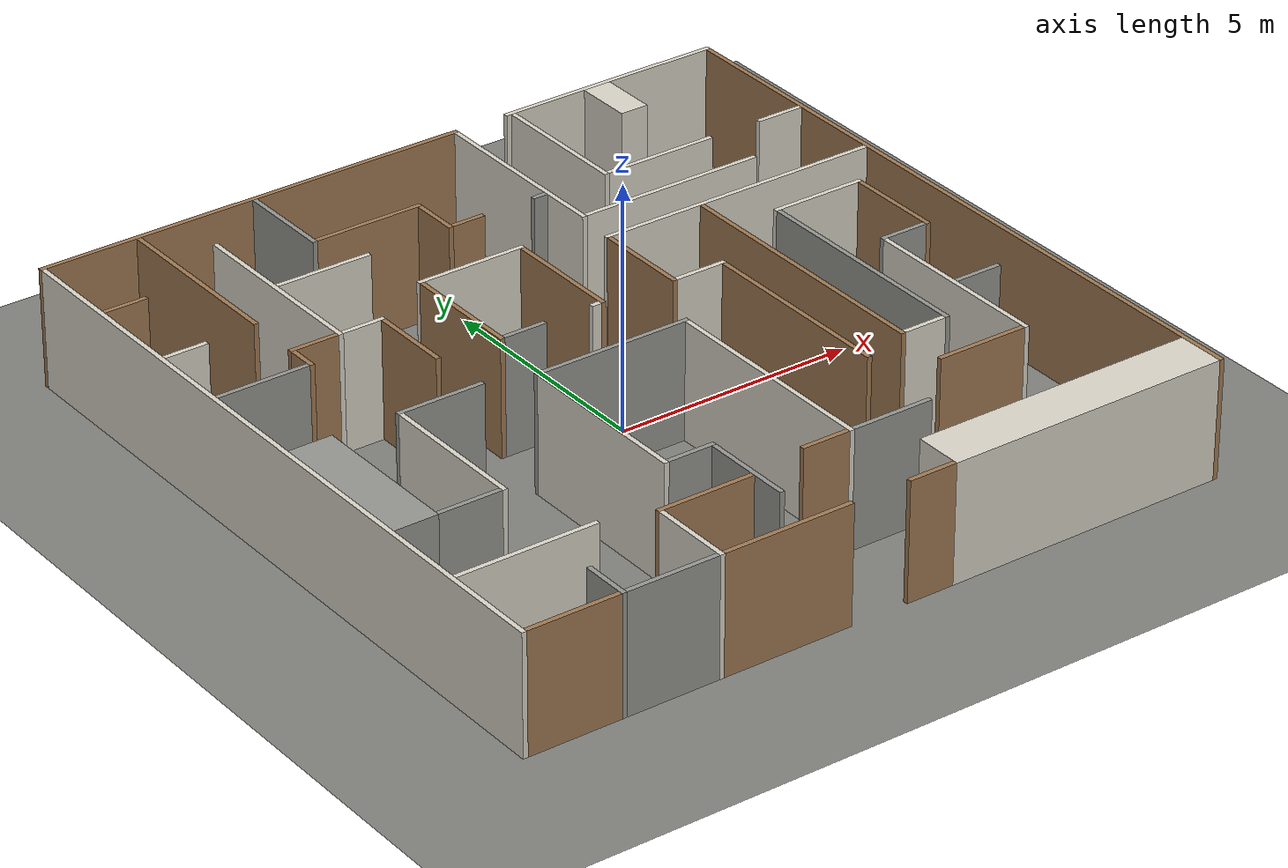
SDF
<?xml version="1.0" ?>
<sdf version="1.9">
  <world name="arena_world">

    <gravity>0 0 -9.8</gravity>

    <physics name="default_physics" type="ode">
      <max_step_size>0.001</max_step_size>
      <real_time_factor>1.0</real_time_factor>
      <real_time_update_rate>1000</real_time_update_rate>
      <ode>
        <solver>
          <type>quick</type>
          <iters>150</iters>
          <sor>1.3</sor>
        </solver>
        <constraints>
          <cfm>0.0</cfm>
          <erp>0.2</erp>
          <contact_max_correcting_vel>100</contact_max_correcting_vel>
          <contact_surface_layer>0.001</contact_surface_layer>
        </constraints>
      </ode>
    </physics>

    <plugin filename="gz-sim-physics-system" name="gz::sim::systems::Physics"></plugin>
    <plugin filename="gz-sim-user-commands-system" name="gz::sim::systems::UserCommands"></plugin>
    <plugin filename="gz-sim-scene-broadcaster-system" name="gz::sim::systems::SceneBroadcaster"></plugin>
    <plugin filename="gz-sim-sensors-system" name="gz::sim::systems::Sensors">
      <render_engine>ogre2</render_engine>
    </plugin>
    <plugin filename="gz-sim-contact-system" name="gz::sim::systems::Contact"></plugin>

    <scene>
      <ambient>0.5 0.5 0.5 1</ambient>
      <background>0.25 0.25 0.28 1</background>
      <shadows>true</shadows>
      <grid>false</grid>
      <origin_visual>false</origin_visual>
    </scene>

    <light type="directional" name="sun">
      <cast_shadows>true</cast_shadows>
      <pose>0 0 15 0 0 0</pose>
      <diffuse>0.85 0.85 0.82 1</diffuse>
      <specular>0.25 0.25 0.25 1</specular>
      <direction>-0.4 0.2 -0.9</direction>
      <attenuation>
        <range>1000</range>
        <constant>0.9</constant>
        <linear>0.01</linear>
        <quadratic>0.001</quadratic>
      </attenuation>
    </light>

    <light type="point" name="ceiling_lamp_00">
      <pose>-2.50 2.50 2.34 0 0 0</pose>
      <diffuse>0.9 0.85 0.7 1</diffuse>
      <specular>0.2 0.2 0.2 1</specular>
      <attenuation>
        <range>6</range>
        <constant>0.6</constant>
        <linear>0.2</linear>
        <quadratic>0.05</quadratic>
      </attenuation>
      <cast_shadows>false</cast_shadows>
    </light>
    <light type="point" name="ceiling_lamp_01">
      <pose>-2.50 -2.50 2.34 0 0 0</pose>
      <diffuse>0.9 0.85 0.7 1</diffuse>
      <specular>0.2 0.2 0.2 1</specular>
      <attenuation>
        <range>6</range>
        <constant>0.6</constant>
        <linear>0.2</linear>
        <quadratic>0.05</quadratic>
      </attenuation>
      <cast_shadows>false</cast_shadows>
    </light>
    <light type="point" name="ceiling_lamp_02">
      <pose>-2.50 -7.50 2.34 0 0 0</pose>
      <diffuse>0.9 0.85 0.7 1</diffuse>
      <specular>0.2 0.2 0.2 1</specular>
      <attenuation>
        <range>6</range>
        <constant>0.6</constant>
        <linear>0.2</linear>
        <quadratic>0.05</quadratic>
      </attenuation>
      <cast_shadows>false</cast_shadows>
    </light>
    <light type="point" name="ceiling_lamp_03">
      <pose>2.50 2.50 2.34 0 0 0</pose>
      <diffuse>0.9 0.85 0.7 1</diffuse>
      <specular>0.2 0.2 0.2 1</specular>
      <attenuation>
        <range>6</range>
        <constant>0.6</constant>
        <linear>0.2</linear>
        <quadratic>0.05</quadratic>
      </attenuation>
      <cast_shadows>false</cast_shadows>
    </light>
    <light type="point" name="ceiling_lamp_04">
      <pose>2.50 -2.50 2.34 0 0 0</pose>
      <diffuse>0.9 0.85 0.7 1</diffuse>
      <specular>0.2 0.2 0.2 1</specular>
      <attenuation>
        <range>6</range>
        <constant>0.6</constant>
        <linear>0.2</linear>
        <quadratic>0.05</quadratic>
      </attenuation>
      <cast_shadows>false</cast_shadows>
    </light>
    <light type="point" name="ceiling_lamp_05">
      <pose>2.50 -7.50 2.34 0 0 0</pose>
      <diffuse>0.9 0.85 0.7 1</diffuse>
      <specular>0.2 0.2 0.2 1</specular>
      <attenuation>
        <range>6</range>
        <constant>0.6</constant>
        <linear>0.2</linear>
        <quadratic>0.05</quadratic>
      </attenuation>
      <cast_shadows>false</cast_shadows>
    </light>
    <light type="point" name="ceiling_lamp_06">
      <pose>7.50 2.50 2.34 0 0 0</pose>
      <diffuse>0.9 0.85 0.7 1</diffuse>
      <specular>0.2 0.2 0.2 1</specular>
      <attenuation>
        <range>6</range>
        <constant>0.6</constant>
        <linear>0.2</linear>
        <quadratic>0.05</quadratic>
      </attenuation>
      <cast_shadows>false</cast_shadows>
    </light>
    <light type="point" name="ceiling_lamp_07">
      <pose>7.50 -2.50 2.34 0 0 0</pose>
      <diffuse>0.9 0.85 0.7 1</diffuse>
      <specular>0.2 0.2 0.2 1</specular>
      <attenuation>
        <range>6</range>
        <constant>0.6</constant>
        <linear>0.2</linear>
        <quadratic>0.05</quadratic>
      </attenuation>
      <cast_shadows>false</cast_shadows>
    </light>
    <light type="point" name="ceiling_lamp_08">
      <pose>7.50 -7.50 2.34 0 0 0</pose>
      <diffuse>0.9 0.85 0.7 1</diffuse>
      <specular>0.2 0.2 0.2 1</specular>
      <attenuation>
        <range>6</range>
        <constant>0.6</constant>
        <linear>0.2</linear>
        <quadratic>0.05</quadratic>
      </attenuation>
      <cast_shadows>false</cast_shadows>
    </light>

    <model name="ground_plane">
      <static>true</static>
      <link name="link">
        <collision name="collision">
          <geometry>
            <plane>
              <normal>0 0 1</normal>
              <size>15.00 15.00</size>
            </plane>
          </geometry>
          <surface>
            <friction>
              <ode>
                <mu>0.8</mu>
                <mu2>0.8</mu2>
              </ode>
            </friction>
            <contact>
              <ode>
                <kp>1e9</kp>
                <kd>1.0</kd>
              </ode>
            </contact>
          </surface>
        </collision>
        <visual name="visual">
          <geometry>
            <plane>
              <normal>0 0 1</normal>
              <size>15.00 15.00</size>
            </plane>
          </geometry>
          <material>
            <ambient>0.45 0.45 0.44 1</ambient>
            <diffuse>0.5 0.5 0.48 1</diffuse>
            <specular>0.15 0.15 0.15 1</specular>
            <pbr>
              <metal>
                <roughness>0.95</roughness>
                <metalness>0.0</metalness>
              </metal>
            </pbr>
          </material>
        </visual>
      </link>
    </model>

    <model name="wall_000">
      <static>true</static>
      <pose>-2.9500 7.4500 1.2200 0 0 0</pose>
      <link name="link">
        <collision name="collision">
          <geometry>
            <box>
              <size>9.1000 0.1000 2.4400</size>
            </box>
          </geometry>
          <surface>
            <friction>
              <ode>
                <mu>0.7</mu>
                <mu2>0.7</mu2>
              </ode>
            </friction>
            <contact>
              <ode>
                <kp>1e9</kp>
                <kd>1.0</kd>
                <max_vel>0.1</max_vel>
                <min_depth>0.001</min_depth>
              </ode>
            </contact>
            <bounce>
              <restitution_coefficient>0.0</restitution_coefficient>
              <threshold>1e6</threshold>
            </bounce>
          </surface>
        </collision>
        <visual name="visual">
          <geometry>
            <box>
              <size>9.1000 0.1000 2.4400</size>
            </box>
          </geometry>
        <material>
          <ambient>0.55 0.42 0.28 1</ambient>
          <diffuse>0.62 0.47 0.32 1</diffuse>
          <specular>0.06 0.06 0.06 1</specular>
          <pbr>
            <metal>
              <albedo_map></albedo_map>
              <roughness>0.7</roughness>
              <metalness>0.0</metalness>
            </metal>
          </pbr>
        </material>
        </visual>
      </link>
    </model>
    <model name="wall_001">
      <static>true</static>
      <pose>5.1000 7.4500 1.2200 0 0 0</pose>
      <link name="link">
        <collision name="collision">
          <geometry>
            <box>
              <size>4.8000 0.1000 2.4400</size>
            </box>
          </geometry>
          <surface>
            <friction>
              <ode>
                <mu>0.7</mu>
                <mu2>0.7</mu2>
              </ode>
            </friction>
            <contact>
              <ode>
                <kp>1e9</kp>
                <kd>1.0</kd>
                <max_vel>0.1</max_vel>
                <min_depth>0.001</min_depth>
              </ode>
            </contact>
            <bounce>
              <restitution_coefficient>0.0</restitution_coefficient>
              <threshold>1e6</threshold>
            </bounce>
          </surface>
        </collision>
        <visual name="visual">
          <geometry>
            <box>
              <size>4.8000 0.1000 2.4400</size>
            </box>
          </geometry>
        <material>
          <ambient>0.82 0.80 0.75 1</ambient>
          <diffuse>0.85 0.83 0.78 1</diffuse>
          <specular>0.05 0.05 0.05 1</specular>
          <pbr>
            <metal>
              <albedo_map></albedo_map>
              <roughness>0.85</roughness>
              <metalness>0.0</metalness>
            </metal>
          </pbr>
        </material>
        </visual>
      </link>
    </model>
    <model name="wall_002">
      <static>true</static>
      <pose>-7.4500 -0.0500 1.2200 0 0 0</pose>
      <link name="link">
        <collision name="collision">
          <geometry>
            <box>
              <size>0.1000 14.9000 2.4400</size>
            </box>
          </geometry>
          <surface>
            <friction>
              <ode>
                <mu>0.7</mu>
                <mu2>0.7</mu2>
              </ode>
            </friction>
            <contact>
              <ode>
                <kp>1e9</kp>
                <kd>1.0</kd>
                <max_vel>0.1</max_vel>
                <min_depth>0.001</min_depth>
              </ode>
            </contact>
            <bounce>
              <restitution_coefficient>0.0</restitution_coefficient>
              <threshold>1e6</threshold>
            </bounce>
          </surface>
        </collision>
        <visual name="visual">
          <geometry>
            <box>
              <size>0.1000 14.9000 2.4400</size>
            </box>
          </geometry>
        <material>
          <ambient>0.82 0.80 0.75 1</ambient>
          <diffuse>0.85 0.83 0.78 1</diffuse>
          <specular>0.05 0.05 0.05 1</specular>
          <pbr>
            <metal>
              <albedo_map></albedo_map>
              <roughness>0.85</roughness>
              <metalness>0.0</metalness>
            </metal>
          </pbr>
        </material>
        </visual>
      </link>
    </model>
    <model name="wall_003">
      <static>true</static>
      <pose>-5.4500 5.4500 1.2200 0 0 0</pose>
      <link name="link">
        <collision name="collision">
          <geometry>
            <box>
              <size>0.1000 3.9000 2.4400</size>
            </box>
          </geometry>
          <surface>
            <friction>
              <ode>
                <mu>0.7</mu>
                <mu2>0.7</mu2>
              </ode>
            </friction>
            <contact>
              <ode>
                <kp>1e9</kp>
                <kd>1.0</kd>
                <max_vel>0.1</max_vel>
                <min_depth>0.001</min_depth>
              </ode>
            </contact>
            <bounce>
              <restitution_coefficient>0.0</restitution_coefficient>
              <threshold>1e6</threshold>
            </bounce>
          </surface>
        </collision>
        <visual name="visual">
          <geometry>
            <box>
              <size>0.1000 3.9000 2.4400</size>
            </box>
          </geometry>
        <material>
          <ambient>0.55 0.42 0.28 1</ambient>
          <diffuse>0.62 0.47 0.32 1</diffuse>
          <specular>0.06 0.06 0.06 1</specular>
          <pbr>
            <metal>
              <albedo_map></albedo_map>
              <roughness>0.7</roughness>
              <metalness>0.0</metalness>
            </metal>
          </pbr>
        </material>
        </visual>
      </link>
    </model>
    <model name="wall_004">
      <static>true</static>
      <pose>-2.9500 6.4000 1.2200 0 0 0</pose>
      <link name="link">
        <collision name="collision">
          <geometry>
            <box>
              <size>0.1000 2.0000 2.4400</size>
            </box>
          </geometry>
          <surface>
            <friction>
              <ode>
                <mu>0.7</mu>
                <mu2>0.7</mu2>
              </ode>
            </friction>
            <contact>
              <ode>
                <kp>1e9</kp>
                <kd>1.0</kd>
                <max_vel>0.1</max_vel>
                <min_depth>0.001</min_depth>
              </ode>
            </contact>
            <bounce>
              <restitution_coefficient>0.0</restitution_coefficient>
              <threshold>1e6</threshold>
            </bounce>
          </surface>
        </collision>
        <visual name="visual">
          <geometry>
            <box>
              <size>0.1000 2.0000 2.4400</size>
            </box>
          </geometry>
        <material>
          <ambient>0.55 0.55 0.53 1</ambient>
          <diffuse>0.58 0.58 0.56 1</diffuse>
          <specular>0.08 0.08 0.08 1</specular>
          <pbr>
            <metal>
              <albedo_map></albedo_map>
              <roughness>0.9</roughness>
              <metalness>0.0</metalness>
            </metal>
          </pbr>
        </material>
        </visual>
      </link>
    </model>
    <model name="wall_005">
      <static>true</static>
      <pose>1.5500 5.3500 1.2200 0 0 0</pose>
      <link name="link">
        <collision name="collision">
          <geometry>
            <box>
              <size>0.1000 4.1000 2.4400</size>
            </box>
          </geometry>
          <surface>
            <friction>
              <ode>
                <mu>0.7</mu>
                <mu2>0.7</mu2>
              </ode>
            </friction>
            <contact>
              <ode>
                <kp>1e9</kp>
                <kd>1.0</kd>
                <max_vel>0.1</max_vel>
                <min_depth>0.001</min_depth>
              </ode>
            </contact>
            <bounce>
              <restitution_coefficient>0.0</restitution_coefficient>
              <threshold>1e6</threshold>
            </bounce>
          </surface>
        </collision>
        <visual name="visual">
          <geometry>
            <box>
              <size>0.1000 4.1000 2.4400</size>
            </box>
          </geometry>
        <material>
          <ambient>0.82 0.80 0.75 1</ambient>
          <diffuse>0.85 0.83 0.78 1</diffuse>
          <specular>0.05 0.05 0.05 1</specular>
          <pbr>
            <metal>
              <albedo_map></albedo_map>
              <roughness>0.85</roughness>
              <metalness>0.0</metalness>
            </metal>
          </pbr>
        </material>
        </visual>
      </link>
    </model>
    <model name="wall_006">
      <static>true</static>
      <pose>2.8500 5.9000 1.2200 0 0 0</pose>
      <link name="link">
        <collision name="collision">
          <geometry>
            <box>
              <size>0.1000 3.0000 2.4400</size>
            </box>
          </geometry>
          <surface>
            <friction>
              <ode>
                <mu>0.7</mu>
                <mu2>0.7</mu2>
              </ode>
            </friction>
            <contact>
              <ode>
                <kp>1e9</kp>
                <kd>1.0</kd>
                <max_vel>0.1</max_vel>
                <min_depth>0.001</min_depth>
              </ode>
            </contact>
            <bounce>
              <restitution_coefficient>0.0</restitution_coefficient>
              <threshold>1e6</threshold>
            </bounce>
          </surface>
        </collision>
        <visual name="visual">
          <geometry>
            <box>
              <size>0.1000 3.0000 2.4400</size>
            </box>
          </geometry>
        <material>
          <ambient>0.82 0.80 0.75 1</ambient>
          <diffuse>0.85 0.83 0.78 1</diffuse>
          <specular>0.05 0.05 0.05 1</specular>
          <pbr>
            <metal>
              <albedo_map></albedo_map>
              <roughness>0.85</roughness>
              <metalness>0.0</metalness>
            </metal>
          </pbr>
        </material>
        </visual>
      </link>
    </model>
    <model name="wall_007">
      <static>true</static>
      <pose>4.8000 6.8000 1.2200 0 0 0</pose>
      <link name="link">
        <collision name="collision">
          <geometry>
            <box>
              <size>0.6000 1.2000 2.4400</size>
            </box>
          </geometry>
          <surface>
            <friction>
              <ode>
                <mu>0.7</mu>
                <mu2>0.7</mu2>
              </ode>
            </friction>
            <contact>
              <ode>
                <kp>1e9</kp>
                <kd>1.0</kd>
                <max_vel>0.1</max_vel>
                <min_depth>0.001</min_depth>
              </ode>
            </contact>
            <bounce>
              <restitution_coefficient>0.0</restitution_coefficient>
              <threshold>1e6</threshold>
            </bounce>
          </surface>
        </collision>
        <visual name="visual">
          <geometry>
            <box>
              <size>0.6000 1.2000 2.4400</size>
            </box>
          </geometry>
        <material>
          <ambient>0.82 0.80 0.75 1</ambient>
          <diffuse>0.85 0.83 0.78 1</diffuse>
          <specular>0.05 0.05 0.05 1</specular>
          <pbr>
            <metal>
              <albedo_map></albedo_map>
              <roughness>0.85</roughness>
              <metalness>0.0</metalness>
            </metal>
          </pbr>
        </material>
        </visual>
      </link>
    </model>
    <model name="wall_008">
      <static>true</static>
      <pose>7.4500 -0.0500 1.2200 0 0 0</pose>
      <link name="link">
        <collision name="collision">
          <geometry>
            <box>
              <size>0.1000 14.9000 2.4400</size>
            </box>
          </geometry>
          <surface>
            <friction>
              <ode>
                <mu>0.7</mu>
                <mu2>0.7</mu2>
              </ode>
            </friction>
            <contact>
              <ode>
                <kp>1e9</kp>
                <kd>1.0</kd>
                <max_vel>0.1</max_vel>
                <min_depth>0.001</min_depth>
              </ode>
            </contact>
            <bounce>
              <restitution_coefficient>0.0</restitution_coefficient>
              <threshold>1e6</threshold>
            </bounce>
          </surface>
        </collision>
        <visual name="visual">
          <geometry>
            <box>
              <size>0.1000 14.9000 2.4400</size>
            </box>
          </geometry>
        <material>
          <ambient>0.55 0.42 0.28 1</ambient>
          <diffuse>0.62 0.47 0.32 1</diffuse>
          <specular>0.06 0.06 0.06 1</specular>
          <pbr>
            <metal>
              <albedo_map></albedo_map>
              <roughness>0.7</roughness>
              <metalness>0.0</metalness>
            </metal>
          </pbr>
        </material>
        </visual>
      </link>
    </model>
    <model name="wall_009">
      <static>true</static>
      <pose>-4.4500 4.3500 1.2200 0 0 0</pose>
      <link name="link">
        <collision name="collision">
          <geometry>
            <box>
              <size>0.1000 4.1000 2.4400</size>
            </box>
          </geometry>
          <surface>
            <friction>
              <ode>
                <mu>0.7</mu>
                <mu2>0.7</mu2>
              </ode>
            </friction>
            <contact>
              <ode>
                <kp>1e9</kp>
                <kd>1.0</kd>
                <max_vel>0.1</max_vel>
                <min_depth>0.001</min_depth>
              </ode>
            </contact>
            <bounce>
              <restitution_coefficient>0.0</restitution_coefficient>
              <threshold>1e6</threshold>
            </bounce>
          </surface>
        </collision>
        <visual name="visual">
          <geometry>
            <box>
              <size>0.1000 4.1000 2.4400</size>
            </box>
          </geometry>
        <material>
          <ambient>0.82 0.80 0.75 1</ambient>
          <diffuse>0.85 0.83 0.78 1</diffuse>
          <specular>0.05 0.05 0.05 1</specular>
          <pbr>
            <metal>
              <albedo_map></albedo_map>
              <roughness>0.85</roughness>
              <metalness>0.0</metalness>
            </metal>
          </pbr>
        </material>
        </visual>
      </link>
    </model>
    <model name="wall_010">
      <static>true</static>
      <pose>-6.9500 5.4500 1.2200 0 0 0</pose>
      <link name="link">
        <collision name="collision">
          <geometry>
            <box>
              <size>0.9000 0.1000 2.4400</size>
            </box>
          </geometry>
          <surface>
            <friction>
              <ode>
                <mu>0.7</mu>
                <mu2>0.7</mu2>
              </ode>
            </friction>
            <contact>
              <ode>
                <kp>1e9</kp>
                <kd>1.0</kd>
                <max_vel>0.1</max_vel>
                <min_depth>0.001</min_depth>
              </ode>
            </contact>
            <bounce>
              <restitution_coefficient>0.0</restitution_coefficient>
              <threshold>1e6</threshold>
            </bounce>
          </surface>
        </collision>
        <visual name="visual">
          <geometry>
            <box>
              <size>0.9000 0.1000 2.4400</size>
            </box>
          </geometry>
        <material>
          <ambient>0.55 0.42 0.28 1</ambient>
          <diffuse>0.62 0.47 0.32 1</diffuse>
          <specular>0.06 0.06 0.06 1</specular>
          <pbr>
            <metal>
              <albedo_map></albedo_map>
              <roughness>0.7</roughness>
              <metalness>0.0</metalness>
            </metal>
          </pbr>
        </material>
        </visual>
      </link>
    </model>
    <model name="wall_011">
      <static>true</static>
      <pose>-1.7500 5.4500 1.2200 0 0 0</pose>
      <link name="link">
        <collision name="collision">
          <geometry>
            <box>
              <size>2.3000 0.1000 2.4400</size>
            </box>
          </geometry>
          <surface>
            <friction>
              <ode>
                <mu>0.7</mu>
                <mu2>0.7</mu2>
              </ode>
            </friction>
            <contact>
              <ode>
                <kp>1e9</kp>
                <kd>1.0</kd>
                <max_vel>0.1</max_vel>
                <min_depth>0.001</min_depth>
              </ode>
            </contact>
            <bounce>
              <restitution_coefficient>0.0</restitution_coefficient>
              <threshold>1e6</threshold>
            </bounce>
          </surface>
        </collision>
        <visual name="visual">
          <geometry>
            <box>
              <size>2.3000 0.1000 2.4400</size>
            </box>
          </geometry>
        <material>
          <ambient>0.55 0.42 0.28 1</ambient>
          <diffuse>0.62 0.47 0.32 1</diffuse>
          <specular>0.06 0.06 0.06 1</specular>
          <pbr>
            <metal>
              <albedo_map></albedo_map>
              <roughness>0.7</roughness>
              <metalness>0.0</metalness>
            </metal>
          </pbr>
        </material>
        </visual>
      </link>
    </model>
    <model name="wall_012">
      <static>true</static>
      <pose>-0.6500 4.9000 1.2200 0 0 0</pose>
      <link name="link">
        <collision name="collision">
          <geometry>
            <box>
              <size>0.1000 1.0000 2.4400</size>
            </box>
          </geometry>
          <surface>
            <friction>
              <ode>
                <mu>0.7</mu>
                <mu2>0.7</mu2>
              </ode>
            </friction>
            <contact>
              <ode>
                <kp>1e9</kp>
                <kd>1.0</kd>
                <max_vel>0.1</max_vel>
                <min_depth>0.001</min_depth>
              </ode>
            </contact>
            <bounce>
              <restitution_coefficient>0.0</restitution_coefficient>
              <threshold>1e6</threshold>
            </bounce>
          </surface>
        </collision>
        <visual name="visual">
          <geometry>
            <box>
              <size>0.1000 1.0000 2.4400</size>
            </box>
          </geometry>
        <material>
          <ambient>0.55 0.42 0.28 1</ambient>
          <diffuse>0.62 0.47 0.32 1</diffuse>
          <specular>0.06 0.06 0.06 1</specular>
          <pbr>
            <metal>
              <albedo_map></albedo_map>
              <roughness>0.7</roughness>
              <metalness>0.0</metalness>
            </metal>
          </pbr>
        </material>
        </visual>
      </link>
    </model>
    <model name="wall_013">
      <static>true</static>
      <pose>-3.4000 4.4500 1.2200 0 0 0</pose>
      <link name="link">
        <collision name="collision">
          <geometry>
            <box>
              <size>2.0000 0.1000 2.4400</size>
            </box>
          </geometry>
          <surface>
            <friction>
              <ode>
                <mu>0.7</mu>
                <mu2>0.7</mu2>
              </ode>
            </friction>
            <contact>
              <ode>
                <kp>1e9</kp>
                <kd>1.0</kd>
                <max_vel>0.1</max_vel>
                <min_depth>0.001</min_depth>
              </ode>
            </contact>
            <bounce>
              <restitution_coefficient>0.0</restitution_coefficient>
              <threshold>1e6</threshold>
            </bounce>
          </surface>
        </collision>
        <visual name="visual">
          <geometry>
            <box>
              <size>2.0000 0.1000 2.4400</size>
            </box>
          </geometry>
        <material>
          <ambient>0.82 0.80 0.75 1</ambient>
          <diffuse>0.85 0.83 0.78 1</diffuse>
          <specular>0.05 0.05 0.05 1</specular>
          <pbr>
            <metal>
              <albedo_map></albedo_map>
              <roughness>0.85</roughness>
              <metalness>0.0</metalness>
            </metal>
          </pbr>
        </material>
        </visual>
      </link>
    </model>
    <model name="wall_014">
      <static>true</static>
      <pose>-0.2500 4.4500 1.2200 0 0 0</pose>
      <link name="link">
        <collision name="collision">
          <geometry>
            <box>
              <size>0.7000 0.1000 2.4400</size>
            </box>
          </geometry>
          <surface>
            <friction>
              <ode>
                <mu>0.7</mu>
                <mu2>0.7</mu2>
              </ode>
            </friction>
            <contact>
              <ode>
                <kp>1e9</kp>
                <kd>1.0</kd>
                <max_vel>0.1</max_vel>
                <min_depth>0.001</min_depth>
              </ode>
            </contact>
            <bounce>
              <restitution_coefficient>0.0</restitution_coefficient>
              <threshold>1e6</threshold>
            </bounce>
          </surface>
        </collision>
        <visual name="visual">
          <geometry>
            <box>
              <size>0.7000 0.1000 2.4400</size>
            </box>
          </geometry>
        <material>
          <ambient>0.55 0.42 0.28 1</ambient>
          <diffuse>0.62 0.47 0.32 1</diffuse>
          <specular>0.06 0.06 0.06 1</specular>
          <pbr>
            <metal>
              <albedo_map></albedo_map>
              <roughness>0.7</roughness>
              <metalness>0.0</metalness>
            </metal>
          </pbr>
        </material>
        </visual>
      </link>
    </model>
    <model name="wall_015">
      <static>true</static>
      <pose>1.3500 4.4500 1.2200 0 0 0</pose>
      <link name="link">
        <collision name="collision">
          <geometry>
            <box>
              <size>0.3000 0.1000 2.4400</size>
            </box>
          </geometry>
          <surface>
            <friction>
              <ode>
                <mu>0.7</mu>
                <mu2>0.7</mu2>
              </ode>
            </friction>
            <contact>
              <ode>
                <kp>1e9</kp>
                <kd>1.0</kd>
                <max_vel>0.1</max_vel>
                <min_depth>0.001</min_depth>
              </ode>
            </contact>
            <bounce>
              <restitution_coefficient>0.0</restitution_coefficient>
              <threshold>1e6</threshold>
            </bounce>
          </surface>
        </collision>
        <visual name="visual">
          <geometry>
            <box>
              <size>0.3000 0.1000 2.4400</size>
            </box>
          </geometry>
        <material>
          <ambient>0.55 0.55 0.53 1</ambient>
          <diffuse>0.58 0.58 0.56 1</diffuse>
          <specular>0.08 0.08 0.08 1</specular>
          <pbr>
            <metal>
              <albedo_map></albedo_map>
              <roughness>0.9</roughness>
              <metalness>0.0</metalness>
            </metal>
          </pbr>
        </material>
        </visual>
      </link>
    </model>
    <model name="wall_016">
      <static>true</static>
      <pose>4.1000 4.4500 1.2200 0 0 0</pose>
      <link name="link">
        <collision name="collision">
          <geometry>
            <box>
              <size>2.4000 0.1000 2.4400</size>
            </box>
          </geometry>
          <surface>
            <friction>
              <ode>
                <mu>0.7</mu>
                <mu2>0.7</mu2>
              </ode>
            </friction>
            <contact>
              <ode>
                <kp>1e9</kp>
                <kd>1.0</kd>
                <max_vel>0.1</max_vel>
                <min_depth>0.001</min_depth>
              </ode>
            </contact>
            <bounce>
              <restitution_coefficient>0.0</restitution_coefficient>
              <threshold>1e6</threshold>
            </bounce>
          </surface>
        </collision>
        <visual name="visual">
          <geometry>
            <box>
              <size>2.4000 0.1000 2.4400</size>
            </box>
          </geometry>
        <material>
          <ambient>0.82 0.80 0.75 1</ambient>
          <diffuse>0.85 0.83 0.78 1</diffuse>
          <specular>0.05 0.05 0.05 1</specular>
          <pbr>
            <metal>
              <albedo_map></albedo_map>
              <roughness>0.85</roughness>
              <metalness>0.0</metalness>
            </metal>
          </pbr>
        </material>
        </visual>
      </link>
    </model>
    <model name="wall_017">
      <static>true</static>
      <pose>6.9000 4.4500 1.2200 0 0 0</pose>
      <link name="link">
        <collision name="collision">
          <geometry>
            <box>
              <size>1.0000 0.1000 2.4400</size>
            </box>
          </geometry>
          <surface>
            <friction>
              <ode>
                <mu>0.7</mu>
                <mu2>0.7</mu2>
              </ode>
            </friction>
            <contact>
              <ode>
                <kp>1e9</kp>
                <kd>1.0</kd>
                <max_vel>0.1</max_vel>
                <min_depth>0.001</min_depth>
              </ode>
            </contact>
            <bounce>
              <restitution_coefficient>0.0</restitution_coefficient>
              <threshold>1e6</threshold>
            </bounce>
          </surface>
        </collision>
        <visual name="visual">
          <geometry>
            <box>
              <size>1.0000 0.1000 2.4400</size>
            </box>
          </geometry>
        <material>
          <ambient>0.82 0.80 0.75 1</ambient>
          <diffuse>0.85 0.83 0.78 1</diffuse>
          <specular>0.05 0.05 0.05 1</specular>
          <pbr>
            <metal>
              <albedo_map></albedo_map>
              <roughness>0.85</roughness>
              <metalness>0.0</metalness>
            </metal>
          </pbr>
        </material>
        </visual>
      </link>
    </model>
    <model name="wall_018">
      <static>true</static>
      <pose>-6.9500 3.4500 1.2200 0 0 0</pose>
      <link name="link">
        <collision name="collision">
          <geometry>
            <box>
              <size>0.9000 0.1000 2.4400</size>
            </box>
          </geometry>
          <surface>
            <friction>
              <ode>
                <mu>0.7</mu>
                <mu2>0.7</mu2>
              </ode>
            </friction>
            <contact>
              <ode>
                <kp>1e9</kp>
                <kd>1.0</kd>
                <max_vel>0.1</max_vel>
                <min_depth>0.001</min_depth>
              </ode>
            </contact>
            <bounce>
              <restitution_coefficient>0.0</restitution_coefficient>
              <threshold>1e6</threshold>
            </bounce>
          </surface>
        </collision>
        <visual name="visual">
          <geometry>
            <box>
              <size>0.9000 0.1000 2.4400</size>
            </box>
          </geometry>
        <material>
          <ambient>0.82 0.80 0.75 1</ambient>
          <diffuse>0.85 0.83 0.78 1</diffuse>
          <specular>0.05 0.05 0.05 1</specular>
          <pbr>
            <metal>
              <albedo_map></albedo_map>
              <roughness>0.85</roughness>
              <metalness>0.0</metalness>
            </metal>
          </pbr>
        </material>
        </visual>
      </link>
    </model>
    <model name="wall_019">
      <static>true</static>
      <pose>3.5500 3.3500 1.2200 0 0 0</pose>
      <link name="link">
        <collision name="collision">
          <geometry>
            <box>
              <size>3.9000 0.1000 2.4400</size>
            </box>
          </geometry>
          <surface>
            <friction>
              <ode>
                <mu>0.7</mu>
                <mu2>0.7</mu2>
              </ode>
            </friction>
            <contact>
              <ode>
                <kp>1e9</kp>
                <kd>1.0</kd>
                <max_vel>0.1</max_vel>
                <min_depth>0.001</min_depth>
              </ode>
            </contact>
            <bounce>
              <restitution_coefficient>0.0</restitution_coefficient>
              <threshold>1e6</threshold>
            </bounce>
          </surface>
        </collision>
        <visual name="visual">
          <geometry>
            <box>
              <size>3.9000 0.1000 2.4400</size>
            </box>
          </geometry>
        <material>
          <ambient>0.82 0.80 0.75 1</ambient>
          <diffuse>0.85 0.83 0.78 1</diffuse>
          <specular>0.05 0.05 0.05 1</specular>
          <pbr>
            <metal>
              <albedo_map></albedo_map>
              <roughness>0.85</roughness>
              <metalness>0.0</metalness>
            </metal>
          </pbr>
        </material>
        </visual>
      </link>
    </model>
    <model name="wall_020">
      <static>true</static>
      <pose>-1.1500 3.0500 1.2200 0 0 0</pose>
      <link name="link">
        <collision name="collision">
          <geometry>
            <box>
              <size>2.3000 0.1000 2.4400</size>
            </box>
          </geometry>
          <surface>
            <friction>
              <ode>
                <mu>0.7</mu>
                <mu2>0.7</mu2>
              </ode>
            </friction>
            <contact>
              <ode>
                <kp>1e9</kp>
                <kd>1.0</kd>
                <max_vel>0.1</max_vel>
                <min_depth>0.001</min_depth>
              </ode>
            </contact>
            <bounce>
              <restitution_coefficient>0.0</restitution_coefficient>
              <threshold>1e6</threshold>
            </bounce>
          </surface>
        </collision>
        <visual name="visual">
          <geometry>
            <box>
              <size>2.3000 0.1000 2.4400</size>
            </box>
          </geometry>
        <material>
          <ambient>0.82 0.80 0.75 1</ambient>
          <diffuse>0.85 0.83 0.78 1</diffuse>
          <specular>0.05 0.05 0.05 1</specular>
          <pbr>
            <metal>
              <albedo_map></albedo_map>
              <roughness>0.85</roughness>
              <metalness>0.0</metalness>
            </metal>
          </pbr>
        </material>
        </visual>
      </link>
    </model>
    <model name="wall_021">
      <static>true</static>
      <pose>-2.2500 1.7500 1.2200 0 0 0</pose>
      <link name="link">
        <collision name="collision">
          <geometry>
            <box>
              <size>0.1000 2.5000 2.4400</size>
            </box>
          </geometry>
          <surface>
            <friction>
              <ode>
                <mu>0.7</mu>
                <mu2>0.7</mu2>
              </ode>
            </friction>
            <contact>
              <ode>
                <kp>1e9</kp>
                <kd>1.0</kd>
                <max_vel>0.1</max_vel>
                <min_depth>0.001</min_depth>
              </ode>
            </contact>
            <bounce>
              <restitution_coefficient>0.0</restitution_coefficient>
              <threshold>1e6</threshold>
            </bounce>
          </surface>
        </collision>
        <visual name="visual">
          <geometry>
            <box>
              <size>0.1000 2.5000 2.4400</size>
            </box>
          </geometry>
        <material>
          <ambient>0.55 0.42 0.28 1</ambient>
          <diffuse>0.62 0.47 0.32 1</diffuse>
          <specular>0.06 0.06 0.06 1</specular>
          <pbr>
            <metal>
              <albedo_map></albedo_map>
              <roughness>0.7</roughness>
              <metalness>0.0</metalness>
            </metal>
          </pbr>
        </material>
        </visual>
      </link>
    </model>
    <model name="wall_022">
      <static>true</static>
      <pose>-0.0500 1.7500 1.2200 0 0 0</pose>
      <link name="link">
        <collision name="collision">
          <geometry>
            <box>
              <size>0.1000 2.5000 2.4400</size>
            </box>
          </geometry>
          <surface>
            <friction>
              <ode>
                <mu>0.7</mu>
                <mu2>0.7</mu2>
              </ode>
            </friction>
            <contact>
              <ode>
                <kp>1e9</kp>
                <kd>1.0</kd>
                <max_vel>0.1</max_vel>
                <min_depth>0.001</min_depth>
              </ode>
            </contact>
            <bounce>
              <restitution_coefficient>0.0</restitution_coefficient>
              <threshold>1e6</threshold>
            </bounce>
          </surface>
        </collision>
        <visual name="visual">
          <geometry>
            <box>
              <size>0.1000 2.5000 2.4400</size>
            </box>
          </geometry>
        <material>
          <ambient>0.55 0.42 0.28 1</ambient>
          <diffuse>0.62 0.47 0.32 1</diffuse>
          <specular>0.06 0.06 0.06 1</specular>
          <pbr>
            <metal>
              <albedo_map></albedo_map>
              <roughness>0.7</roughness>
              <metalness>0.0</metalness>
            </metal>
          </pbr>
        </material>
        </visual>
      </link>
    </model>
    <model name="wall_023">
      <static>true</static>
      <pose>4.4000 2.4500 1.2200 0 0 0</pose>
      <link name="link">
        <collision name="collision">
          <geometry>
            <box>
              <size>6.0000 0.1000 2.4400</size>
            </box>
          </geometry>
          <surface>
            <friction>
              <ode>
                <mu>0.7</mu>
                <mu2>0.7</mu2>
              </ode>
            </friction>
            <contact>
              <ode>
                <kp>1e9</kp>
                <kd>1.0</kd>
                <max_vel>0.1</max_vel>
                <min_depth>0.001</min_depth>
              </ode>
            </contact>
            <bounce>
              <restitution_coefficient>0.0</restitution_coefficient>
              <threshold>1e6</threshold>
            </bounce>
          </surface>
        </collision>
        <visual name="visual">
          <geometry>
            <box>
              <size>6.0000 0.1000 2.4400</size>
            </box>
          </geometry>
        <material>
          <ambient>0.82 0.80 0.75 1</ambient>
          <diffuse>0.85 0.83 0.78 1</diffuse>
          <specular>0.05 0.05 0.05 1</specular>
          <pbr>
            <metal>
              <albedo_map></albedo_map>
              <roughness>0.85</roughness>
              <metalness>0.0</metalness>
            </metal>
          </pbr>
        </material>
        </visual>
      </link>
    </model>
    <model name="wall_024">
      <static>true</static>
      <pose>-5.0000 2.3500 1.2200 0 0 0</pose>
      <link name="link">
        <collision name="collision">
          <geometry>
            <box>
              <size>1.0000 0.1000 2.4400</size>
            </box>
          </geometry>
          <surface>
            <friction>
              <ode>
                <mu>0.7</mu>
                <mu2>0.7</mu2>
              </ode>
            </friction>
            <contact>
              <ode>
                <kp>1e9</kp>
                <kd>1.0</kd>
                <max_vel>0.1</max_vel>
                <min_depth>0.001</min_depth>
              </ode>
            </contact>
            <bounce>
              <restitution_coefficient>0.0</restitution_coefficient>
              <threshold>1e6</threshold>
            </bounce>
          </surface>
        </collision>
        <visual name="visual">
          <geometry>
            <box>
              <size>1.0000 0.1000 2.4400</size>
            </box>
          </geometry>
        <material>
          <ambient>0.55 0.42 0.28 1</ambient>
          <diffuse>0.62 0.47 0.32 1</diffuse>
          <specular>0.06 0.06 0.06 1</specular>
          <pbr>
            <metal>
              <albedo_map></albedo_map>
              <roughness>0.7</roughness>
              <metalness>0.0</metalness>
            </metal>
          </pbr>
        </material>
        </visual>
      </link>
    </model>
    <model name="wall_025">
      <static>true</static>
      <pose>-3.9500 2.3500 1.2200 0 0 0</pose>
      <link name="link">
        <collision name="collision">
          <geometry>
            <box>
              <size>0.9000 0.1000 2.4400</size>
            </box>
          </geometry>
          <surface>
            <friction>
              <ode>
                <mu>0.7</mu>
                <mu2>0.7</mu2>
              </ode>
            </friction>
            <contact>
              <ode>
                <kp>1e9</kp>
                <kd>1.0</kd>
                <max_vel>0.1</max_vel>
                <min_depth>0.001</min_depth>
              </ode>
            </contact>
            <bounce>
              <restitution_coefficient>0.0</restitution_coefficient>
              <threshold>1e6</threshold>
            </bounce>
          </surface>
        </collision>
        <visual name="visual">
          <geometry>
            <box>
              <size>0.9000 0.1000 2.4400</size>
            </box>
          </geometry>
        <material>
          <ambient>0.82 0.80 0.75 1</ambient>
          <diffuse>0.85 0.83 0.78 1</diffuse>
          <specular>0.05 0.05 0.05 1</specular>
          <pbr>
            <metal>
              <albedo_map></albedo_map>
              <roughness>0.85</roughness>
              <metalness>0.0</metalness>
            </metal>
          </pbr>
        </material>
        </visual>
      </link>
    </model>
    <model name="wall_026">
      <static>true</static>
      <pose>1.4500 1.4000 1.2200 0 0 0</pose>
      <link name="link">
        <collision name="collision">
          <geometry>
            <box>
              <size>0.1000 2.0000 2.4400</size>
            </box>
          </geometry>
          <surface>
            <friction>
              <ode>
                <mu>0.7</mu>
                <mu2>0.7</mu2>
              </ode>
            </friction>
            <contact>
              <ode>
                <kp>1e9</kp>
                <kd>1.0</kd>
                <max_vel>0.1</max_vel>
                <min_depth>0.001</min_depth>
              </ode>
            </contact>
            <bounce>
              <restitution_coefficient>0.0</restitution_coefficient>
              <threshold>1e6</threshold>
            </bounce>
          </surface>
        </collision>
        <visual name="visual">
          <geometry>
            <box>
              <size>0.1000 2.0000 2.4400</size>
            </box>
          </geometry>
        <material>
          <ambient>0.55 0.42 0.28 1</ambient>
          <diffuse>0.62 0.47 0.32 1</diffuse>
          <specular>0.06 0.06 0.06 1</specular>
          <pbr>
            <metal>
              <albedo_map></albedo_map>
              <roughness>0.7</roughness>
              <metalness>0.0</metalness>
            </metal>
          </pbr>
        </material>
        </visual>
      </link>
    </model>
    <model name="wall_027">
      <static>true</static>
      <pose>3.5500 -0.5500 1.2200 0 0 0</pose>
      <link name="link">
        <collision name="collision">
          <geometry>
            <box>
              <size>0.1000 5.9000 2.4400</size>
            </box>
          </geometry>
          <surface>
            <friction>
              <ode>
                <mu>0.7</mu>
                <mu2>0.7</mu2>
              </ode>
            </friction>
            <contact>
              <ode>
                <kp>1e9</kp>
                <kd>1.0</kd>
                <max_vel>0.1</max_vel>
                <min_depth>0.001</min_depth>
              </ode>
            </contact>
            <bounce>
              <restitution_coefficient>0.0</restitution_coefficient>
              <threshold>1e6</threshold>
            </bounce>
          </surface>
        </collision>
        <visual name="visual">
          <geometry>
            <box>
              <size>0.1000 5.9000 2.4400</size>
            </box>
          </geometry>
        <material>
          <ambient>0.55 0.42 0.28 1</ambient>
          <diffuse>0.62 0.47 0.32 1</diffuse>
          <specular>0.06 0.06 0.06 1</specular>
          <pbr>
            <metal>
              <albedo_map></albedo_map>
              <roughness>0.7</roughness>
              <metalness>0.0</metalness>
            </metal>
          </pbr>
        </material>
        </visual>
      </link>
    </model>
    <model name="wall_028">
      <static>true</static>
      <pose>-5.4500 2.0000 1.2200 0 0 0</pose>
      <link name="link">
        <collision name="collision">
          <geometry>
            <box>
              <size>0.1000 0.6000 2.4400</size>
            </box>
          </geometry>
          <surface>
            <friction>
              <ode>
                <mu>0.7</mu>
                <mu2>0.7</mu2>
              </ode>
            </friction>
            <contact>
              <ode>
                <kp>1e9</kp>
                <kd>1.0</kd>
                <max_vel>0.1</max_vel>
                <min_depth>0.001</min_depth>
              </ode>
            </contact>
            <bounce>
              <restitution_coefficient>0.0</restitution_coefficient>
              <threshold>1e6</threshold>
            </bounce>
          </surface>
        </collision>
        <visual name="visual">
          <geometry>
            <box>
              <size>0.1000 0.6000 2.4400</size>
            </box>
          </geometry>
        <material>
          <ambient>0.55 0.42 0.28 1</ambient>
          <diffuse>0.62 0.47 0.32 1</diffuse>
          <specular>0.06 0.06 0.06 1</specular>
          <pbr>
            <metal>
              <albedo_map></albedo_map>
              <roughness>0.7</roughness>
              <metalness>0.0</metalness>
            </metal>
          </pbr>
        </material>
        </visual>
      </link>
    </model>
    <model name="wall_029">
      <static>true</static>
      <pose>-3.5500 1.4500 1.2200 0 0 0</pose>
      <link name="link">
        <collision name="collision">
          <geometry>
            <box>
              <size>0.1000 1.7000 2.4400</size>
            </box>
          </geometry>
          <surface>
            <friction>
              <ode>
                <mu>0.7</mu>
                <mu2>0.7</mu2>
              </ode>
            </friction>
            <contact>
              <ode>
                <kp>1e9</kp>
                <kd>1.0</kd>
                <max_vel>0.1</max_vel>
                <min_depth>0.001</min_depth>
              </ode>
            </contact>
            <bounce>
              <restitution_coefficient>0.0</restitution_coefficient>
              <threshold>1e6</threshold>
            </bounce>
          </surface>
        </collision>
        <visual name="visual">
          <geometry>
            <box>
              <size>0.1000 1.7000 2.4400</size>
            </box>
          </geometry>
        <material>
          <ambient>0.55 0.42 0.28 1</ambient>
          <diffuse>0.62 0.47 0.32 1</diffuse>
          <specular>0.06 0.06 0.06 1</specular>
          <pbr>
            <metal>
              <albedo_map></albedo_map>
              <roughness>0.7</roughness>
              <metalness>0.0</metalness>
            </metal>
          </pbr>
        </material>
        </visual>
      </link>
    </model>
    <model name="wall_030">
      <static>true</static>
      <pose>-6.4500 1.7500 1.2200 0 0 0</pose>
      <link name="link">
        <collision name="collision">
          <geometry>
            <box>
              <size>1.9000 0.1000 2.4400</size>
            </box>
          </geometry>
          <surface>
            <friction>
              <ode>
                <mu>0.7</mu>
                <mu2>0.7</mu2>
              </ode>
            </friction>
            <contact>
              <ode>
                <kp>1e9</kp>
                <kd>1.0</kd>
                <max_vel>0.1</max_vel>
                <min_depth>0.001</min_depth>
              </ode>
            </contact>
            <bounce>
              <restitution_coefficient>0.0</restitution_coefficient>
              <threshold>1e6</threshold>
            </bounce>
          </surface>
        </collision>
        <visual name="visual">
          <geometry>
            <box>
              <size>1.9000 0.1000 2.4400</size>
            </box>
          </geometry>
        <material>
          <ambient>0.55 0.55 0.53 1</ambient>
          <diffuse>0.58 0.58 0.56 1</diffuse>
          <specular>0.08 0.08 0.08 1</specular>
          <pbr>
            <metal>
              <albedo_map></albedo_map>
              <roughness>0.9</roughness>
              <metalness>0.0</metalness>
            </metal>
          </pbr>
        </material>
        </visual>
      </link>
    </model>
    <model name="wall_031">
      <static>true</static>
      <pose>5.5000 1.4500 1.2200 0 0 0</pose>
      <link name="link">
        <collision name="collision">
          <geometry>
            <box>
              <size>2.0000 0.1000 2.4400</size>
            </box>
          </geometry>
          <surface>
            <friction>
              <ode>
                <mu>0.7</mu>
                <mu2>0.7</mu2>
              </ode>
            </friction>
            <contact>
              <ode>
                <kp>1e9</kp>
                <kd>1.0</kd>
                <max_vel>0.1</max_vel>
                <min_depth>0.001</min_depth>
              </ode>
            </contact>
            <bounce>
              <restitution_coefficient>0.0</restitution_coefficient>
              <threshold>1e6</threshold>
            </bounce>
          </surface>
        </collision>
        <visual name="visual">
          <geometry>
            <box>
              <size>2.0000 0.1000 2.4400</size>
            </box>
          </geometry>
        <material>
          <ambient>0.82 0.80 0.75 1</ambient>
          <diffuse>0.85 0.83 0.78 1</diffuse>
          <specular>0.05 0.05 0.05 1</specular>
          <pbr>
            <metal>
              <albedo_map></albedo_map>
              <roughness>0.85</roughness>
              <metalness>0.0</metalness>
            </metal>
          </pbr>
        </material>
        </visual>
      </link>
    </model>
    <model name="wall_032">
      <static>true</static>
      <pose>4.5500 -1.0500 1.2200 0 0 0</pose>
      <link name="link">
        <collision name="collision">
          <geometry>
            <box>
              <size>0.1000 4.9000 2.4400</size>
            </box>
          </geometry>
          <surface>
            <friction>
              <ode>
                <mu>0.7</mu>
                <mu2>0.7</mu2>
              </ode>
            </friction>
            <contact>
              <ode>
                <kp>1e9</kp>
                <kd>1.0</kd>
                <max_vel>0.1</max_vel>
                <min_depth>0.001</min_depth>
              </ode>
            </contact>
            <bounce>
              <restitution_coefficient>0.0</restitution_coefficient>
              <threshold>1e6</threshold>
            </bounce>
          </surface>
        </collision>
        <visual name="visual">
          <geometry>
            <box>
              <size>0.1000 4.9000 2.4400</size>
            </box>
          </geometry>
        <material>
          <ambient>0.55 0.55 0.53 1</ambient>
          <diffuse>0.58 0.58 0.56 1</diffuse>
          <specular>0.08 0.08 0.08 1</specular>
          <pbr>
            <metal>
              <albedo_map></albedo_map>
              <roughness>0.9</roughness>
              <metalness>0.0</metalness>
            </metal>
          </pbr>
        </material>
        </visual>
      </link>
    </model>
    <model name="wall_033">
      <static>true</static>
      <pose>6.4500 0.4000 1.2200 0 0 0</pose>
      <link name="link">
        <collision name="collision">
          <geometry>
            <box>
              <size>0.1000 2.0000 2.4400</size>
            </box>
          </geometry>
          <surface>
            <friction>
              <ode>
                <mu>0.7</mu>
                <mu2>0.7</mu2>
              </ode>
            </friction>
            <contact>
              <ode>
                <kp>1e9</kp>
                <kd>1.0</kd>
                <max_vel>0.1</max_vel>
                <min_depth>0.001</min_depth>
              </ode>
            </contact>
            <bounce>
              <restitution_coefficient>0.0</restitution_coefficient>
              <threshold>1e6</threshold>
            </bounce>
          </surface>
        </collision>
        <visual name="visual">
          <geometry>
            <box>
              <size>0.1000 2.0000 2.4400</size>
            </box>
          </geometry>
        <material>
          <ambient>0.55 0.42 0.28 1</ambient>
          <diffuse>0.62 0.47 0.32 1</diffuse>
          <specular>0.06 0.06 0.06 1</specular>
          <pbr>
            <metal>
              <albedo_map></albedo_map>
              <roughness>0.7</roughness>
              <metalness>0.0</metalness>
            </metal>
          </pbr>
        </material>
        </visual>
      </link>
    </model>
    <model name="wall_034">
      <static>true</static>
      <pose>-1.7500 0.5500 1.2200 0 0 0</pose>
      <link name="link">
        <collision name="collision">
          <geometry>
            <box>
              <size>0.9000 0.1000 2.4400</size>
            </box>
          </geometry>
          <surface>
            <friction>
              <ode>
                <mu>0.7</mu>
                <mu2>0.7</mu2>
              </ode>
            </friction>
            <contact>
              <ode>
                <kp>1e9</kp>
                <kd>1.0</kd>
                <max_vel>0.1</max_vel>
                <min_depth>0.001</min_depth>
              </ode>
            </contact>
            <bounce>
              <restitution_coefficient>0.0</restitution_coefficient>
              <threshold>1e6</threshold>
            </bounce>
          </surface>
        </collision>
        <visual name="visual">
          <geometry>
            <box>
              <size>0.9000 0.1000 2.4400</size>
            </box>
          </geometry>
        <material>
          <ambient>0.55 0.55 0.53 1</ambient>
          <diffuse>0.58 0.58 0.56 1</diffuse>
          <specular>0.08 0.08 0.08 1</specular>
          <pbr>
            <metal>
              <albedo_map></albedo_map>
              <roughness>0.9</roughness>
              <metalness>0.0</metalness>
            </metal>
          </pbr>
        </material>
        </visual>
      </link>
    </model>
    <model name="wall_035">
      <static>true</static>
      <pose>-0.2000 0.5500 1.2200 0 0 0</pose>
      <link name="link">
        <collision name="collision">
          <geometry>
            <box>
              <size>0.2000 0.1000 2.4400</size>
            </box>
          </geometry>
          <surface>
            <friction>
              <ode>
                <mu>0.7</mu>
                <mu2>0.7</mu2>
              </ode>
            </friction>
            <contact>
              <ode>
                <kp>1e9</kp>
                <kd>1.0</kd>
                <max_vel>0.1</max_vel>
                <min_depth>0.001</min_depth>
              </ode>
            </contact>
            <bounce>
              <restitution_coefficient>0.0</restitution_coefficient>
              <threshold>1e6</threshold>
            </bounce>
          </surface>
        </collision>
        <visual name="visual">
          <geometry>
            <box>
              <size>0.2000 0.1000 2.4400</size>
            </box>
          </geometry>
        <material>
          <ambient>0.82 0.80 0.75 1</ambient>
          <diffuse>0.85 0.83 0.78 1</diffuse>
          <specular>0.05 0.05 0.05 1</specular>
          <pbr>
            <metal>
              <albedo_map></albedo_map>
              <roughness>0.85</roughness>
              <metalness>0.0</metalness>
            </metal>
          </pbr>
        </material>
        </visual>
      </link>
    </model>
    <model name="wall_036">
      <static>true</static>
      <pose>2.0500 0.4500 1.2200 0 0 0</pose>
      <link name="link">
        <collision name="collision">
          <geometry>
            <box>
              <size>1.1000 0.1000 2.4400</size>
            </box>
          </geometry>
          <surface>
            <friction>
              <ode>
                <mu>0.7</mu>
                <mu2>0.7</mu2>
              </ode>
            </friction>
            <contact>
              <ode>
                <kp>1e9</kp>
                <kd>1.0</kd>
                <max_vel>0.1</max_vel>
                <min_depth>0.001</min_depth>
              </ode>
            </contact>
            <bounce>
              <restitution_coefficient>0.0</restitution_coefficient>
              <threshold>1e6</threshold>
            </bounce>
          </surface>
        </collision>
        <visual name="visual">
          <geometry>
            <box>
              <size>1.1000 0.1000 2.4400</size>
            </box>
          </geometry>
        <material>
          <ambient>0.82 0.80 0.75 1</ambient>
          <diffuse>0.85 0.83 0.78 1</diffuse>
          <specular>0.05 0.05 0.05 1</specular>
          <pbr>
            <metal>
              <albedo_map></albedo_map>
              <roughness>0.85</roughness>
              <metalness>0.0</metalness>
            </metal>
          </pbr>
        </material>
        </visual>
      </link>
    </model>
    <model name="wall_037">
      <static>true</static>
      <pose>2.5500 -1.7000 1.2200 0 0 0</pose>
      <link name="link">
        <collision name="collision">
          <geometry>
            <box>
              <size>0.1000 4.2000 2.4400</size>
            </box>
          </geometry>
          <surface>
            <friction>
              <ode>
                <mu>0.7</mu>
                <mu2>0.7</mu2>
              </ode>
            </friction>
            <contact>
              <ode>
                <kp>1e9</kp>
                <kd>1.0</kd>
                <max_vel>0.1</max_vel>
                <min_depth>0.001</min_depth>
              </ode>
            </contact>
            <bounce>
              <restitution_coefficient>0.0</restitution_coefficient>
              <threshold>1e6</threshold>
            </bounce>
          </surface>
        </collision>
        <visual name="visual">
          <geometry>
            <box>
              <size>0.1000 4.2000 2.4400</size>
            </box>
          </geometry>
        <material>
          <ambient>0.55 0.42 0.28 1</ambient>
          <diffuse>0.62 0.47 0.32 1</diffuse>
          <specular>0.06 0.06 0.06 1</specular>
          <pbr>
            <metal>
              <albedo_map></albedo_map>
              <roughness>0.7</roughness>
              <metalness>0.0</metalness>
            </metal>
          </pbr>
        </material>
        </visual>
      </link>
    </model>
    <model name="wall_038">
      <static>true</static>
      <pose>-6.9500 -2.1000 1.2200 0 0 0</pose>
      <link name="link">
        <collision name="collision">
          <geometry>
            <box>
              <size>0.9000 3.2000 2.4400</size>
            </box>
          </geometry>
          <surface>
            <friction>
              <ode>
                <mu>0.7</mu>
                <mu2>0.7</mu2>
              </ode>
            </friction>
            <contact>
              <ode>
                <kp>1e9</kp>
                <kd>1.0</kd>
                <max_vel>0.1</max_vel>
                <min_depth>0.001</min_depth>
              </ode>
            </contact>
            <bounce>
              <restitution_coefficient>0.0</restitution_coefficient>
              <threshold>1e6</threshold>
            </bounce>
          </surface>
        </collision>
        <visual name="visual">
          <geometry>
            <box>
              <size>0.9000 3.2000 2.4400</size>
            </box>
          </geometry>
        <material>
          <ambient>0.55 0.55 0.53 1</ambient>
          <diffuse>0.58 0.58 0.56 1</diffuse>
          <specular>0.08 0.08 0.08 1</specular>
          <pbr>
            <metal>
              <albedo_map></albedo_map>
              <roughness>0.9</roughness>
              <metalness>0.0</metalness>
            </metal>
          </pbr>
        </material>
        </visual>
      </link>
    </model>
    <model name="wall_039">
      <static>true</static>
      <pose>-4.3000 -0.5500 1.2200 0 0 0</pose>
      <link name="link">
        <collision name="collision">
          <geometry>
            <box>
              <size>1.8000 0.1000 2.4400</size>
            </box>
          </geometry>
          <surface>
            <friction>
              <ode>
                <mu>0.7</mu>
                <mu2>0.7</mu2>
              </ode>
            </friction>
            <contact>
              <ode>
                <kp>1e9</kp>
                <kd>1.0</kd>
                <max_vel>0.1</max_vel>
                <min_depth>0.001</min_depth>
              </ode>
            </contact>
            <bounce>
              <restitution_coefficient>0.0</restitution_coefficient>
              <threshold>1e6</threshold>
            </bounce>
          </surface>
        </collision>
        <visual name="visual">
          <geometry>
            <box>
              <size>1.8000 0.1000 2.4400</size>
            </box>
          </geometry>
        <material>
          <ambient>0.55 0.55 0.53 1</ambient>
          <diffuse>0.58 0.58 0.56 1</diffuse>
          <specular>0.08 0.08 0.08 1</specular>
          <pbr>
            <metal>
              <albedo_map></albedo_map>
              <roughness>0.9</roughness>
              <metalness>0.0</metalness>
            </metal>
          </pbr>
        </material>
        </visual>
      </link>
    </model>
    <model name="wall_040">
      <static>true</static>
      <pose>5.9000 -0.5500 1.2200 0 0 0</pose>
      <link name="link">
        <collision name="collision">
          <geometry>
            <box>
              <size>1.0000 0.1000 2.4400</size>
            </box>
          </geometry>
          <surface>
            <friction>
              <ode>
                <mu>0.7</mu>
                <mu2>0.7</mu2>
              </ode>
            </friction>
            <contact>
              <ode>
                <kp>1e9</kp>
                <kd>1.0</kd>
                <max_vel>0.1</max_vel>
                <min_depth>0.001</min_depth>
              </ode>
            </contact>
            <bounce>
              <restitution_coefficient>0.0</restitution_coefficient>
              <threshold>1e6</threshold>
            </bounce>
          </surface>
        </collision>
        <visual name="visual">
          <geometry>
            <box>
              <size>1.0000 0.1000 2.4400</size>
            </box>
          </geometry>
        <material>
          <ambient>0.55 0.55 0.53 1</ambient>
          <diffuse>0.58 0.58 0.56 1</diffuse>
          <specular>0.08 0.08 0.08 1</specular>
          <pbr>
            <metal>
              <albedo_map></albedo_map>
              <roughness>0.9</roughness>
              <metalness>0.0</metalness>
            </metal>
          </pbr>
        </material>
        </visual>
      </link>
    </model>
    <model name="wall_041">
      <static>true</static>
      <pose>-5.1500 -2.1500 1.2200 0 0 0</pose>
      <link name="link">
        <collision name="collision">
          <geometry>
            <box>
              <size>0.1000 3.1000 2.4400</size>
            </box>
          </geometry>
          <surface>
            <friction>
              <ode>
                <mu>0.7</mu>
                <mu2>0.7</mu2>
              </ode>
            </friction>
            <contact>
              <ode>
                <kp>1e9</kp>
                <kd>1.0</kd>
                <max_vel>0.1</max_vel>
                <min_depth>0.001</min_depth>
              </ode>
            </contact>
            <bounce>
              <restitution_coefficient>0.0</restitution_coefficient>
              <threshold>1e6</threshold>
            </bounce>
          </surface>
        </collision>
        <visual name="visual">
          <geometry>
            <box>
              <size>0.1000 3.1000 2.4400</size>
            </box>
          </geometry>
        <material>
          <ambient>0.82 0.80 0.75 1</ambient>
          <diffuse>0.85 0.83 0.78 1</diffuse>
          <specular>0.05 0.05 0.05 1</specular>
          <pbr>
            <metal>
              <albedo_map></albedo_map>
              <roughness>0.85</roughness>
              <metalness>0.0</metalness>
            </metal>
          </pbr>
        </material>
        </visual>
      </link>
    </model>
    <model name="wall_042">
      <static>true</static>
      <pose>5.4500 -2.6000 1.2200 0 0 0</pose>
      <link name="link">
        <collision name="collision">
          <geometry>
            <box>
              <size>0.1000 4.0000 2.4400</size>
            </box>
          </geometry>
          <surface>
            <friction>
              <ode>
                <mu>0.7</mu>
                <mu2>0.7</mu2>
              </ode>
            </friction>
            <contact>
              <ode>
                <kp>1e9</kp>
                <kd>1.0</kd>
                <max_vel>0.1</max_vel>
                <min_depth>0.001</min_depth>
              </ode>
            </contact>
            <bounce>
              <restitution_coefficient>0.0</restitution_coefficient>
              <threshold>1e6</threshold>
            </bounce>
          </surface>
        </collision>
        <visual name="visual">
          <geometry>
            <box>
              <size>0.1000 4.0000 2.4400</size>
            </box>
          </geometry>
        <material>
          <ambient>0.82 0.80 0.75 1</ambient>
          <diffuse>0.85 0.83 0.78 1</diffuse>
          <specular>0.05 0.05 0.05 1</specular>
          <pbr>
            <metal>
              <albedo_map></albedo_map>
              <roughness>0.85</roughness>
              <metalness>0.0</metalness>
            </metal>
          </pbr>
        </material>
        </visual>
      </link>
    </model>
    <model name="wall_043">
      <static>true</static>
      <pose>-0.8500 -0.8500 1.2200 0 0 0</pose>
      <link name="link">
        <collision name="collision">
          <geometry>
            <box>
              <size>3.3000 0.1000 2.4400</size>
            </box>
          </geometry>
          <surface>
            <friction>
              <ode>
                <mu>0.7</mu>
                <mu2>0.7</mu2>
              </ode>
            </friction>
            <contact>
              <ode>
                <kp>1e9</kp>
                <kd>1.0</kd>
                <max_vel>0.1</max_vel>
                <min_depth>0.001</min_depth>
              </ode>
            </contact>
            <bounce>
              <restitution_coefficient>0.0</restitution_coefficient>
              <threshold>1e6</threshold>
            </bounce>
          </surface>
        </collision>
        <visual name="visual">
          <geometry>
            <box>
              <size>3.3000 0.1000 2.4400</size>
            </box>
          </geometry>
        <material>
          <ambient>0.55 0.55 0.53 1</ambient>
          <diffuse>0.58 0.58 0.56 1</diffuse>
          <specular>0.08 0.08 0.08 1</specular>
          <pbr>
            <metal>
              <albedo_map></albedo_map>
              <roughness>0.9</roughness>
              <metalness>0.0</metalness>
            </metal>
          </pbr>
        </material>
        </visual>
      </link>
    </model>
    <model name="wall_044">
      <static>true</static>
      <pose>-2.4500 -2.7500 1.2200 0 0 0</pose>
      <link name="link">
        <collision name="collision">
          <geometry>
            <box>
              <size>0.1000 3.7000 2.4400</size>
            </box>
          </geometry>
          <surface>
            <friction>
              <ode>
                <mu>0.7</mu>
                <mu2>0.7</mu2>
              </ode>
            </friction>
            <contact>
              <ode>
                <kp>1e9</kp>
                <kd>1.0</kd>
                <max_vel>0.1</max_vel>
                <min_depth>0.001</min_depth>
              </ode>
            </contact>
            <bounce>
              <restitution_coefficient>0.0</restitution_coefficient>
              <threshold>1e6</threshold>
            </bounce>
          </surface>
        </collision>
        <visual name="visual">
          <geometry>
            <box>
              <size>0.1000 3.7000 2.4400</size>
            </box>
          </geometry>
        <material>
          <ambient>0.82 0.80 0.75 1</ambient>
          <diffuse>0.85 0.83 0.78 1</diffuse>
          <specular>0.05 0.05 0.05 1</specular>
          <pbr>
            <metal>
              <albedo_map></albedo_map>
              <roughness>0.85</roughness>
              <metalness>0.0</metalness>
            </metal>
          </pbr>
        </material>
        </visual>
      </link>
    </model>
    <model name="wall_045">
      <static>true</static>
      <pose>0.7500 -3.2500 1.2200 0 0 0</pose>
      <link name="link">
        <collision name="collision">
          <geometry>
            <box>
              <size>0.1000 4.7000 2.4400</size>
            </box>
          </geometry>
          <surface>
            <friction>
              <ode>
                <mu>0.7</mu>
                <mu2>0.7</mu2>
              </ode>
            </friction>
            <contact>
              <ode>
                <kp>1e9</kp>
                <kd>1.0</kd>
                <max_vel>0.1</max_vel>
                <min_depth>0.001</min_depth>
              </ode>
            </contact>
            <bounce>
              <restitution_coefficient>0.0</restitution_coefficient>
              <threshold>1e6</threshold>
            </bounce>
          </surface>
        </collision>
        <visual name="visual">
          <geometry>
            <box>
              <size>0.1000 4.7000 2.4400</size>
            </box>
          </geometry>
        <material>
          <ambient>0.82 0.80 0.75 1</ambient>
          <diffuse>0.85 0.83 0.78 1</diffuse>
          <specular>0.05 0.05 0.05 1</specular>
          <pbr>
            <metal>
              <albedo_map></albedo_map>
              <roughness>0.85</roughness>
              <metalness>0.0</metalness>
            </metal>
          </pbr>
        </material>
        </visual>
      </link>
    </model>
    <model name="wall_046">
      <static>true</static>
      <pose>6.0000 -2.5500 1.2200 0 0 0</pose>
      <link name="link">
        <collision name="collision">
          <geometry>
            <box>
              <size>1.0000 0.1000 2.4400</size>
            </box>
          </geometry>
          <surface>
            <friction>
              <ode>
                <mu>0.7</mu>
                <mu2>0.7</mu2>
              </ode>
            </friction>
            <contact>
              <ode>
                <kp>1e9</kp>
                <kd>1.0</kd>
                <max_vel>0.1</max_vel>
                <min_depth>0.001</min_depth>
              </ode>
            </contact>
            <bounce>
              <restitution_coefficient>0.0</restitution_coefficient>
              <threshold>1e6</threshold>
            </bounce>
          </surface>
        </collision>
        <visual name="visual">
          <geometry>
            <box>
              <size>1.0000 0.1000 2.4400</size>
            </box>
          </geometry>
        <material>
          <ambient>0.55 0.55 0.53 1</ambient>
          <diffuse>0.58 0.58 0.56 1</diffuse>
          <specular>0.08 0.08 0.08 1</specular>
          <pbr>
            <metal>
              <albedo_map></albedo_map>
              <roughness>0.9</roughness>
              <metalness>0.0</metalness>
            </metal>
          </pbr>
        </material>
        </visual>
      </link>
    </model>
    <model name="wall_047">
      <static>true</static>
      <pose>4.0500 -3.4500 1.2200 0 0 0</pose>
      <link name="link">
        <collision name="collision">
          <geometry>
            <box>
              <size>0.9000 0.1000 2.4400</size>
            </box>
          </geometry>
          <surface>
            <friction>
              <ode>
                <mu>0.7</mu>
                <mu2>0.7</mu2>
              </ode>
            </friction>
            <contact>
              <ode>
                <kp>1e9</kp>
                <kd>1.0</kd>
                <max_vel>0.1</max_vel>
                <min_depth>0.001</min_depth>
              </ode>
            </contact>
            <bounce>
              <restitution_coefficient>0.0</restitution_coefficient>
              <threshold>1e6</threshold>
            </bounce>
          </surface>
        </collision>
        <visual name="visual">
          <geometry>
            <box>
              <size>0.9000 0.1000 2.4400</size>
            </box>
          </geometry>
        <material>
          <ambient>0.82 0.80 0.75 1</ambient>
          <diffuse>0.85 0.83 0.78 1</diffuse>
          <specular>0.05 0.05 0.05 1</specular>
          <pbr>
            <metal>
              <albedo_map></albedo_map>
              <roughness>0.85</roughness>
              <metalness>0.0</metalness>
            </metal>
          </pbr>
        </material>
        </visual>
      </link>
    </model>
    <model name="wall_048">
      <static>true</static>
      <pose>-5.8500 -3.6500 1.2200 0 0 0</pose>
      <link name="link">
        <collision name="collision">
          <geometry>
            <box>
              <size>1.3000 0.1000 2.4400</size>
            </box>
          </geometry>
          <surface>
            <friction>
              <ode>
                <mu>0.7</mu>
                <mu2>0.7</mu2>
              </ode>
            </friction>
            <contact>
              <ode>
                <kp>1e9</kp>
                <kd>1.0</kd>
                <max_vel>0.1</max_vel>
                <min_depth>0.001</min_depth>
              </ode>
            </contact>
            <bounce>
              <restitution_coefficient>0.0</restitution_coefficient>
              <threshold>1e6</threshold>
            </bounce>
          </surface>
        </collision>
        <visual name="visual">
          <geometry>
            <box>
              <size>1.3000 0.1000 2.4400</size>
            </box>
          </geometry>
        <material>
          <ambient>0.55 0.55 0.53 1</ambient>
          <diffuse>0.58 0.58 0.56 1</diffuse>
          <specular>0.08 0.08 0.08 1</specular>
          <pbr>
            <metal>
              <albedo_map></albedo_map>
              <roughness>0.9</roughness>
              <metalness>0.0</metalness>
            </metal>
          </pbr>
        </material>
        </visual>
      </link>
    </model>
    <model name="wall_049">
      <static>true</static>
      <pose>-1.9000 -4.5500 1.2200 0 0 0</pose>
      <link name="link">
        <collision name="collision">
          <geometry>
            <box>
              <size>1.0000 0.1000 2.4400</size>
            </box>
          </geometry>
          <surface>
            <friction>
              <ode>
                <mu>0.7</mu>
                <mu2>0.7</mu2>
              </ode>
            </friction>
            <contact>
              <ode>
                <kp>1e9</kp>
                <kd>1.0</kd>
                <max_vel>0.1</max_vel>
                <min_depth>0.001</min_depth>
              </ode>
            </contact>
            <bounce>
              <restitution_coefficient>0.0</restitution_coefficient>
              <threshold>1e6</threshold>
            </bounce>
          </surface>
        </collision>
        <visual name="visual">
          <geometry>
            <box>
              <size>1.0000 0.1000 2.4400</size>
            </box>
          </geometry>
        <material>
          <ambient>0.55 0.55 0.53 1</ambient>
          <diffuse>0.58 0.58 0.56 1</diffuse>
          <specular>0.08 0.08 0.08 1</specular>
          <pbr>
            <metal>
              <albedo_map></albedo_map>
              <roughness>0.9</roughness>
              <metalness>0.0</metalness>
            </metal>
          </pbr>
        </material>
        </visual>
      </link>
    </model>
    <model name="wall_050">
      <static>true</static>
      <pose>4.4500 -4.5500 1.2200 0 0 0</pose>
      <link name="link">
        <collision name="collision">
          <geometry>
            <box>
              <size>1.9000 0.1000 2.4400</size>
            </box>
          </geometry>
          <surface>
            <friction>
              <ode>
                <mu>0.7</mu>
                <mu2>0.7</mu2>
              </ode>
            </friction>
            <contact>
              <ode>
                <kp>1e9</kp>
                <kd>1.0</kd>
                <max_vel>0.1</max_vel>
                <min_depth>0.001</min_depth>
              </ode>
            </contact>
            <bounce>
              <restitution_coefficient>0.0</restitution_coefficient>
              <threshold>1e6</threshold>
            </bounce>
          </surface>
        </collision>
        <visual name="visual">
          <geometry>
            <box>
              <size>1.9000 0.1000 2.4400</size>
            </box>
          </geometry>
        <material>
          <ambient>0.55 0.42 0.28 1</ambient>
          <diffuse>0.62 0.47 0.32 1</diffuse>
          <specular>0.06 0.06 0.06 1</specular>
          <pbr>
            <metal>
              <albedo_map></albedo_map>
              <roughness>0.7</roughness>
              <metalness>0.0</metalness>
            </metal>
          </pbr>
        </material>
        </visual>
      </link>
    </model>
    <model name="wall_051">
      <static>true</static>
      <pose>-1.4500 -5.5500 1.2200 0 0 0</pose>
      <link name="link">
        <collision name="collision">
          <geometry>
            <box>
              <size>0.1000 1.9000 2.4400</size>
            </box>
          </geometry>
          <surface>
            <friction>
              <ode>
                <mu>0.7</mu>
                <mu2>0.7</mu2>
              </ode>
            </friction>
            <contact>
              <ode>
                <kp>1e9</kp>
                <kd>1.0</kd>
                <max_vel>0.1</max_vel>
                <min_depth>0.001</min_depth>
              </ode>
            </contact>
            <bounce>
              <restitution_coefficient>0.0</restitution_coefficient>
              <threshold>1e6</threshold>
            </bounce>
          </surface>
        </collision>
        <visual name="visual">
          <geometry>
            <box>
              <size>0.1000 1.9000 2.4400</size>
            </box>
          </geometry>
        <material>
          <ambient>0.55 0.55 0.53 1</ambient>
          <diffuse>0.58 0.58 0.56 1</diffuse>
          <specular>0.08 0.08 0.08 1</specular>
          <pbr>
            <metal>
              <albedo_map></albedo_map>
              <roughness>0.9</roughness>
              <metalness>0.0</metalness>
            </metal>
          </pbr>
        </material>
        </visual>
      </link>
    </model>
    <model name="wall_052">
      <static>true</static>
      <pose>-5.9500 -5.4500 1.2200 0 0 0</pose>
      <link name="link">
        <collision name="collision">
          <geometry>
            <box>
              <size>2.9000 0.1000 2.4400</size>
            </box>
          </geometry>
          <surface>
            <friction>
              <ode>
                <mu>0.7</mu>
                <mu2>0.7</mu2>
              </ode>
            </friction>
            <contact>
              <ode>
                <kp>1e9</kp>
                <kd>1.0</kd>
                <max_vel>0.1</max_vel>
                <min_depth>0.001</min_depth>
              </ode>
            </contact>
            <bounce>
              <restitution_coefficient>0.0</restitution_coefficient>
              <threshold>1e6</threshold>
            </bounce>
          </surface>
        </collision>
        <visual name="visual">
          <geometry>
            <box>
              <size>2.9000 0.1000 2.4400</size>
            </box>
          </geometry>
        <material>
          <ambient>0.82 0.80 0.75 1</ambient>
          <diffuse>0.85 0.83 0.78 1</diffuse>
          <specular>0.05 0.05 0.05 1</specular>
          <pbr>
            <metal>
              <albedo_map></albedo_map>
              <roughness>0.85</roughness>
              <metalness>0.0</metalness>
            </metal>
          </pbr>
        </material>
        </visual>
      </link>
    </model>
    <model name="wall_053">
      <static>true</static>
      <pose>0.2000 -5.5500 1.2200 0 0 0</pose>
      <link name="link">
        <collision name="collision">
          <geometry>
            <box>
              <size>1.0000 0.1000 2.4400</size>
            </box>
          </geometry>
          <surface>
            <friction>
              <ode>
                <mu>0.7</mu>
                <mu2>0.7</mu2>
              </ode>
            </friction>
            <contact>
              <ode>
                <kp>1e9</kp>
                <kd>1.0</kd>
                <max_vel>0.1</max_vel>
                <min_depth>0.001</min_depth>
              </ode>
            </contact>
            <bounce>
              <restitution_coefficient>0.0</restitution_coefficient>
              <threshold>1e6</threshold>
            </bounce>
          </surface>
        </collision>
        <visual name="visual">
          <geometry>
            <box>
              <size>1.0000 0.1000 2.4400</size>
            </box>
          </geometry>
        <material>
          <ambient>0.55 0.42 0.28 1</ambient>
          <diffuse>0.62 0.47 0.32 1</diffuse>
          <specular>0.06 0.06 0.06 1</specular>
          <pbr>
            <metal>
              <albedo_map></albedo_map>
              <roughness>0.7</roughness>
              <metalness>0.0</metalness>
            </metal>
          </pbr>
        </material>
        </visual>
      </link>
    </model>
    <model name="wall_054">
      <static>true</static>
      <pose>1.6500 -5.5500 1.2200 0 0 0</pose>
      <link name="link">
        <collision name="collision">
          <geometry>
            <box>
              <size>1.7000 0.1000 2.4400</size>
            </box>
          </geometry>
          <surface>
            <friction>
              <ode>
                <mu>0.7</mu>
                <mu2>0.7</mu2>
              </ode>
            </friction>
            <contact>
              <ode>
                <kp>1e9</kp>
                <kd>1.0</kd>
                <max_vel>0.1</max_vel>
                <min_depth>0.001</min_depth>
              </ode>
            </contact>
            <bounce>
              <restitution_coefficient>0.0</restitution_coefficient>
              <threshold>1e6</threshold>
            </bounce>
          </surface>
        </collision>
        <visual name="visual">
          <geometry>
            <box>
              <size>1.7000 0.1000 2.4400</size>
            </box>
          </geometry>
        <material>
          <ambient>0.55 0.55 0.53 1</ambient>
          <diffuse>0.58 0.58 0.56 1</diffuse>
          <specular>0.08 0.08 0.08 1</specular>
          <pbr>
            <metal>
              <albedo_map></albedo_map>
              <roughness>0.9</roughness>
              <metalness>0.0</metalness>
            </metal>
          </pbr>
        </material>
        </visual>
      </link>
    </model>
    <model name="wall_055">
      <static>true</static>
      <pose>-2.5000 -5.7500 1.2200 0 0 0</pose>
      <link name="link">
        <collision name="collision">
          <geometry>
            <box>
              <size>2.0000 0.1000 2.4400</size>
            </box>
          </geometry>
          <surface>
            <friction>
              <ode>
                <mu>0.7</mu>
                <mu2>0.7</mu2>
              </ode>
            </friction>
            <contact>
              <ode>
                <kp>1e9</kp>
                <kd>1.0</kd>
                <max_vel>0.1</max_vel>
                <min_depth>0.001</min_depth>
              </ode>
            </contact>
            <bounce>
              <restitution_coefficient>0.0</restitution_coefficient>
              <threshold>1e6</threshold>
            </bounce>
          </surface>
        </collision>
        <visual name="visual">
          <geometry>
            <box>
              <size>2.0000 0.1000 2.4400</size>
            </box>
          </geometry>
        <material>
          <ambient>0.55 0.42 0.28 1</ambient>
          <diffuse>0.62 0.47 0.32 1</diffuse>
          <specular>0.06 0.06 0.06 1</specular>
          <pbr>
            <metal>
              <albedo_map></albedo_map>
              <roughness>0.7</roughness>
              <metalness>0.0</metalness>
            </metal>
          </pbr>
        </material>
        </visual>
      </link>
    </model>
    <model name="wall_056">
      <static>true</static>
      <pose>-3.4500 -6.6500 1.2200 0 0 0</pose>
      <link name="link">
        <collision name="collision">
          <geometry>
            <box>
              <size>0.1000 1.7000 2.4400</size>
            </box>
          </geometry>
          <surface>
            <friction>
              <ode>
                <mu>0.7</mu>
                <mu2>0.7</mu2>
              </ode>
            </friction>
            <contact>
              <ode>
                <kp>1e9</kp>
                <kd>1.0</kd>
                <max_vel>0.1</max_vel>
                <min_depth>0.001</min_depth>
              </ode>
            </contact>
            <bounce>
              <restitution_coefficient>0.0</restitution_coefficient>
              <threshold>1e6</threshold>
            </bounce>
          </surface>
        </collision>
        <visual name="visual">
          <geometry>
            <box>
              <size>0.1000 1.7000 2.4400</size>
            </box>
          </geometry>
        <material>
          <ambient>0.82 0.80 0.75 1</ambient>
          <diffuse>0.85 0.83 0.78 1</diffuse>
          <specular>0.05 0.05 0.05 1</specular>
          <pbr>
            <metal>
              <albedo_map></albedo_map>
              <roughness>0.85</roughness>
              <metalness>0.0</metalness>
            </metal>
          </pbr>
        </material>
        </visual>
      </link>
    </model>
    <model name="wall_057">
      <static>true</static>
      <pose>-5.4500 -7.0000 1.2200 0 0 0</pose>
      <link name="link">
        <collision name="collision">
          <geometry>
            <box>
              <size>0.1000 1.0000 2.4400</size>
            </box>
          </geometry>
          <surface>
            <friction>
              <ode>
                <mu>0.7</mu>
                <mu2>0.7</mu2>
              </ode>
            </friction>
            <contact>
              <ode>
                <kp>1e9</kp>
                <kd>1.0</kd>
                <max_vel>0.1</max_vel>
                <min_depth>0.001</min_depth>
              </ode>
            </contact>
            <bounce>
              <restitution_coefficient>0.0</restitution_coefficient>
              <threshold>1e6</threshold>
            </bounce>
          </surface>
        </collision>
        <visual name="visual">
          <geometry>
            <box>
              <size>0.1000 1.0000 2.4400</size>
            </box>
          </geometry>
        <material>
          <ambient>0.55 0.55 0.53 1</ambient>
          <diffuse>0.58 0.58 0.56 1</diffuse>
          <specular>0.08 0.08 0.08 1</specular>
          <pbr>
            <metal>
              <albedo_map></albedo_map>
              <roughness>0.9</roughness>
              <metalness>0.0</metalness>
            </metal>
          </pbr>
        </material>
        </visual>
      </link>
    </model>
    <model name="wall_058">
      <static>true</static>
      <pose>4.4500 -7.0000 1.2200 0 0 0</pose>
      <link name="link">
        <collision name="collision">
          <geometry>
            <box>
              <size>5.9000 1.0000 2.4400</size>
            </box>
          </geometry>
          <surface>
            <friction>
              <ode>
                <mu>0.7</mu>
                <mu2>0.7</mu2>
              </ode>
            </friction>
            <contact>
              <ode>
                <kp>1e9</kp>
                <kd>1.0</kd>
                <max_vel>0.1</max_vel>
                <min_depth>0.001</min_depth>
              </ode>
            </contact>
            <bounce>
              <restitution_coefficient>0.0</restitution_coefficient>
              <threshold>1e6</threshold>
            </bounce>
          </surface>
        </collision>
        <visual name="visual">
          <geometry>
            <box>
              <size>5.9000 1.0000 2.4400</size>
            </box>
          </geometry>
        <material>
          <ambient>0.82 0.80 0.75 1</ambient>
          <diffuse>0.85 0.83 0.78 1</diffuse>
          <specular>0.05 0.05 0.05 1</specular>
          <pbr>
            <metal>
              <albedo_map></albedo_map>
              <roughness>0.85</roughness>
              <metalness>0.0</metalness>
            </metal>
          </pbr>
        </material>
        </visual>
      </link>
    </model>
    <model name="wall_059">
      <static>true</static>
      <pose>-6.4500 -7.4500 1.2200 0 0 0</pose>
      <link name="link">
        <collision name="collision">
          <geometry>
            <box>
              <size>1.9000 0.1000 2.4400</size>
            </box>
          </geometry>
          <surface>
            <friction>
              <ode>
                <mu>0.7</mu>
                <mu2>0.7</mu2>
              </ode>
            </friction>
            <contact>
              <ode>
                <kp>1e9</kp>
                <kd>1.0</kd>
                <max_vel>0.1</max_vel>
                <min_depth>0.001</min_depth>
              </ode>
            </contact>
            <bounce>
              <restitution_coefficient>0.0</restitution_coefficient>
              <threshold>1e6</threshold>
            </bounce>
          </surface>
        </collision>
        <visual name="visual">
          <geometry>
            <box>
              <size>1.9000 0.1000 2.4400</size>
            </box>
          </geometry>
        <material>
          <ambient>0.55 0.42 0.28 1</ambient>
          <diffuse>0.62 0.47 0.32 1</diffuse>
          <specular>0.06 0.06 0.06 1</specular>
          <pbr>
            <metal>
              <albedo_map></albedo_map>
              <roughness>0.7</roughness>
              <metalness>0.0</metalness>
            </metal>
          </pbr>
        </material>
        </visual>
      </link>
    </model>
    <model name="wall_060">
      <static>true</static>
      <pose>-4.4500 -7.4500 1.2200 0 0 0</pose>
      <link name="link">
        <collision name="collision">
          <geometry>
            <box>
              <size>1.9000 0.1000 2.4400</size>
            </box>
          </geometry>
          <surface>
            <friction>
              <ode>
                <mu>0.7</mu>
                <mu2>0.7</mu2>
              </ode>
            </friction>
            <contact>
              <ode>
                <kp>1e9</kp>
                <kd>1.0</kd>
                <max_vel>0.1</max_vel>
                <min_depth>0.001</min_depth>
              </ode>
            </contact>
            <bounce>
              <restitution_coefficient>0.0</restitution_coefficient>
              <threshold>1e6</threshold>
            </bounce>
          </surface>
        </collision>
        <visual name="visual">
          <geometry>
            <box>
              <size>1.9000 0.1000 2.4400</size>
            </box>
          </geometry>
        <material>
          <ambient>0.55 0.55 0.53 1</ambient>
          <diffuse>0.58 0.58 0.56 1</diffuse>
          <specular>0.08 0.08 0.08 1</specular>
          <pbr>
            <metal>
              <albedo_map></albedo_map>
              <roughness>0.9</roughness>
              <metalness>0.0</metalness>
            </metal>
          </pbr>
        </material>
        </visual>
      </link>
    </model>
    <model name="wall_061">
      <static>true</static>
      <pose>-2.0500 -7.4500 1.2200 0 0 0</pose>
      <link name="link">
        <collision name="collision">
          <geometry>
            <box>
              <size>2.7000 0.1000 2.4400</size>
            </box>
          </geometry>
          <surface>
            <friction>
              <ode>
                <mu>0.7</mu>
                <mu2>0.7</mu2>
              </ode>
            </friction>
            <contact>
              <ode>
                <kp>1e9</kp>
                <kd>1.0</kd>
                <max_vel>0.1</max_vel>
                <min_depth>0.001</min_depth>
              </ode>
            </contact>
            <bounce>
              <restitution_coefficient>0.0</restitution_coefficient>
              <threshold>1e6</threshold>
            </bounce>
          </surface>
        </collision>
        <visual name="visual">
          <geometry>
            <box>
              <size>2.7000 0.1000 2.4400</size>
            </box>
          </geometry>
        <material>
          <ambient>0.55 0.42 0.28 1</ambient>
          <diffuse>0.62 0.47 0.32 1</diffuse>
          <specular>0.06 0.06 0.06 1</specular>
          <pbr>
            <metal>
              <albedo_map></albedo_map>
              <roughness>0.7</roughness>
              <metalness>0.0</metalness>
            </metal>
          </pbr>
        </material>
        </visual>
      </link>
    </model>
    <model name="wall_062">
      <static>true</static>
      <pose>1.0000 -7.4500 1.2200 0 0 0</pose>
      <link name="link">
        <collision name="collision">
          <geometry>
            <box>
              <size>1.0000 0.1000 2.4400</size>
            </box>
          </geometry>
          <surface>
            <friction>
              <ode>
                <mu>0.7</mu>
                <mu2>0.7</mu2>
              </ode>
            </friction>
            <contact>
              <ode>
                <kp>1e9</kp>
                <kd>1.0</kd>
                <max_vel>0.1</max_vel>
                <min_depth>0.001</min_depth>
              </ode>
            </contact>
            <bounce>
              <restitution_coefficient>0.0</restitution_coefficient>
              <threshold>1e6</threshold>
            </bounce>
          </surface>
        </collision>
        <visual name="visual">
          <geometry>
            <box>
              <size>1.0000 0.1000 2.4400</size>
            </box>
          </geometry>
        <material>
          <ambient>0.55 0.42 0.28 1</ambient>
          <diffuse>0.62 0.47 0.32 1</diffuse>
          <specular>0.06 0.06 0.06 1</specular>
          <pbr>
            <metal>
              <albedo_map></albedo_map>
              <roughness>0.7</roughness>
              <metalness>0.0</metalness>
            </metal>
          </pbr>
        </material>
        </visual>
      </link>
    </model>

    <gui fullscreen="0">
      <plugin filename="MinimalScene" name="3D View">
        <gz-gui>
          <title>3D View</title>
          <property type="bool" key="showTitleBar">false</property>
          <property type="string" key="state">docked</property>
        </gz-gui>
        <engine>ogre2</engine>
        <scene>scene</scene>
        <ambient_light>0.5 0.5 0.5</ambient_light>
        <background_color>0.25 0.25 0.28</background_color>
        <camera_pose>0 -10 8 0 0.5 1.57</camera_pose>
      </plugin>
      <plugin filename="GzSceneManager" name="Scene Manager">
        <gz-gui>
          <property key="resizable" type="bool">false</property>
          <property key="width" type="double">5</property>
          <property key="height" type="double">5</property>
          <property key="state" type="string">floating</property>
          <property key="showTitleBar" type="bool">false</property>
        </gz-gui>
      </plugin>
      <plugin filename="InteractiveViewControl" name="Interactive view control">
        <gz-gui>
          <property key="resizable" type="bool">false</property>
          <property key="width" type="double">5</property>
          <property key="height" type="double">5</property>
          <property key="state" type="string">floating</property>
          <property key="showTitleBar" type="bool">false</property>
        </gz-gui>
      </plugin>
      <plugin filename="WorldControl" name="World control">
        <gz-gui>
          <title>World control</title>
          <property type="bool" key="showTitleBar">false</property>
          <property type="bool" key="resizable">false</property>
          <property type="double" key="height">72</property>
          <property type="double" key="width">121</property>
          <property type="string" key="state">floating</property>
          <anchors target="3D View">
            <line own="left" target="left"/>
            <line own="bottom" target="bottom"/>
          </anchors>
        </gz-gui>
        <play_pause>true</play_pause>
        <step>true</step>
        <start_paused>true</start_paused>
      </plugin>
      <plugin filename="WorldStats" name="World stats">
        <gz-gui>
          <title>World stats</title>
          <property type="bool" key="showTitleBar">false</property>
          <property type="bool" key="resizable">false</property>
          <property type="double" key="height">110</property>
          <property type="double" key="width">290</property>
          <property type="string" key="state">floating</property>
          <anchors target="3D View">
            <line own="right" target="right"/>
            <line own="bottom" target="bottom"/>
          </anchors>
        </gz-gui>
        <sim_time>true</sim_time>
        <real_time>true</real_time>
        <real_time_factor>true</real_time_factor>
        <iterations>true</iterations>
      </plugin>
    </gui>

  </world>
</sdf>
